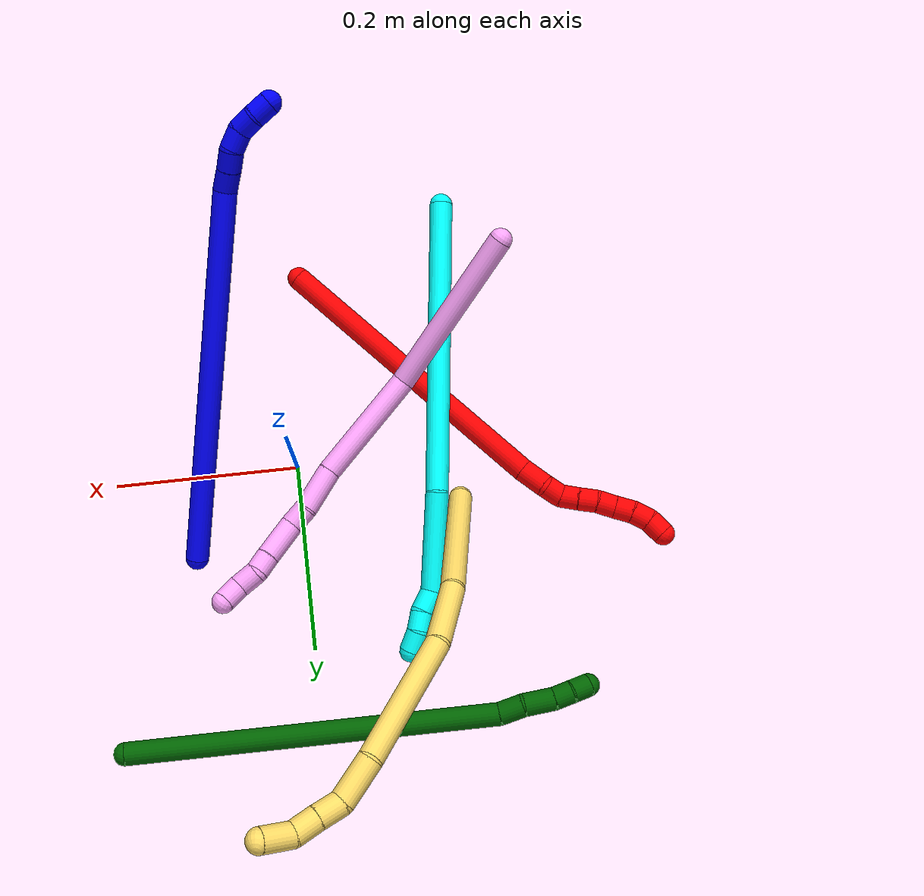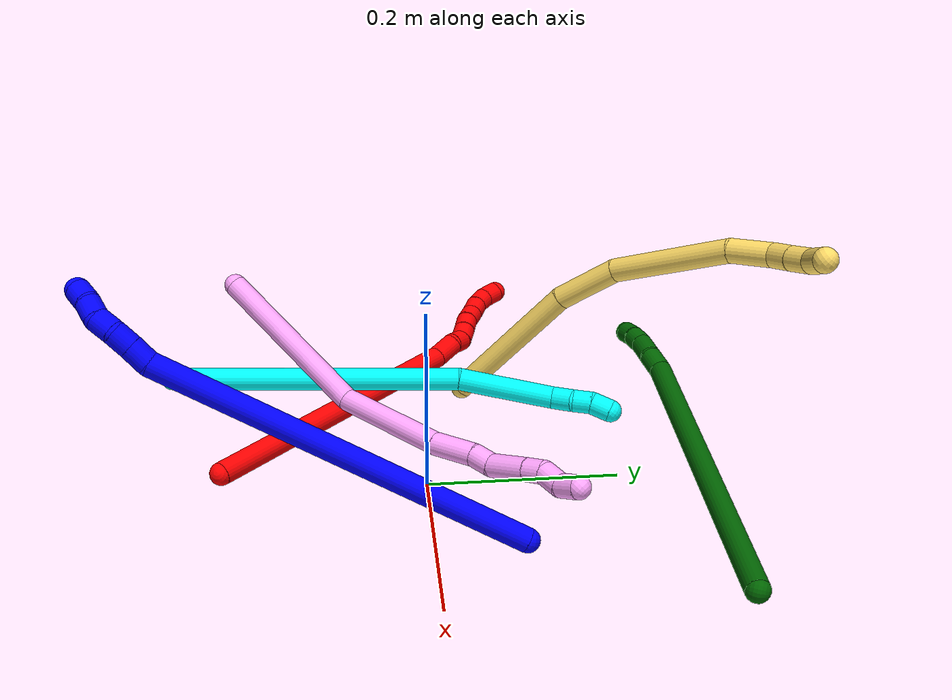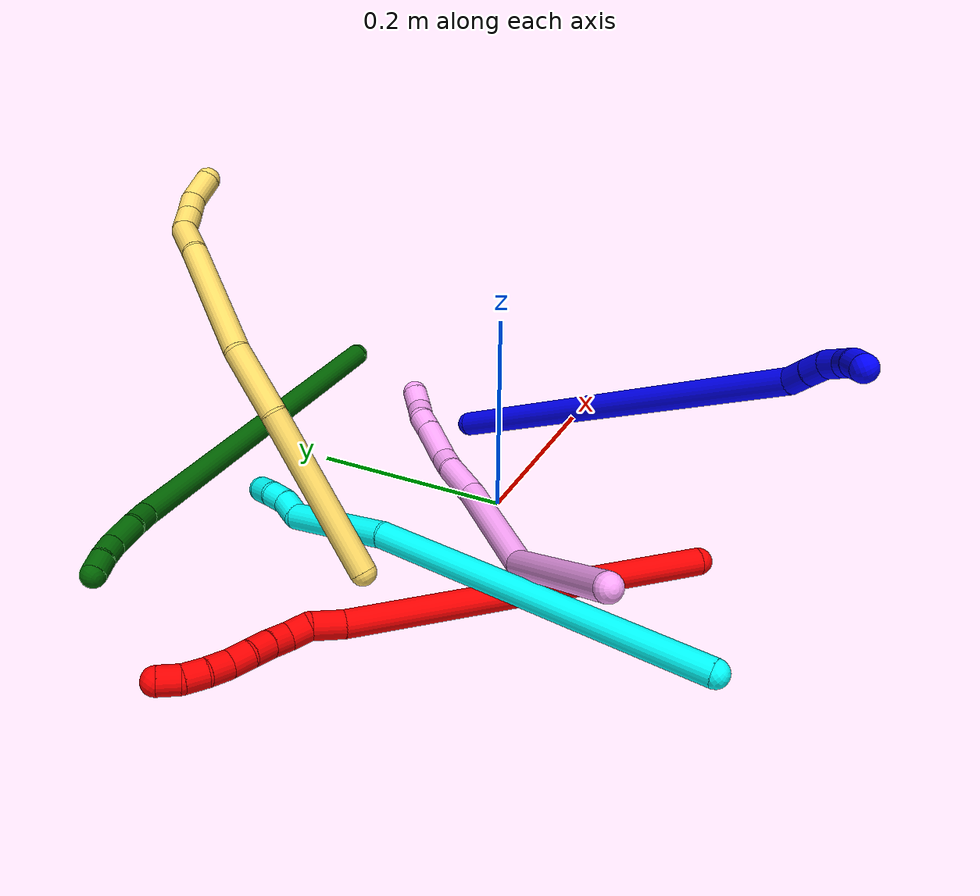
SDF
<sdf version="1.7">
 <world name="default">
  <plugin name="TubeGeneratorPlugin" filename="libtube_generator_plugin.so"/>
  <model name="photoneo_s_sensor">
   <static>1</static>
   <pose>0 0 2 1.57079 1.57079 3.14159</pose>
   <link name="link">
    <inertial><mass>0.1</mass></inertial>
    <sensor name="sensor" type="depth">
     <update_rate>30</update_rate>
     <camera>
      <horizontal_fov>1.22</horizontal_fov>
      <image><width>1920</width><height>1200</height><format>B8G8R8</format></image>
      <clip><near>0.1</near><far>4</far></clip>
      <depth_camera><output>points</output></depth_camera>
     </camera>
     <plugin name="camera_plugin" filename="libgazebo_ros_depth_camera.so">
      <baseline>0.2</baseline>
      <alwaysOn>1</alwaysOn>
      <updateRate>0.0</updateRate>
      <cameraName>camera_ir</cameraName>
      <imageTopicName>/camera/color/image_raw</imageTopicName>
      <cameraInfoTopicName>/camera/color/camera_info</cameraInfoTopicName>
      <depthImageTopicName>/camera/depth/image_raw</depthImageTopicName>
      <depthImageCameraInfoTopicName>/camera/depth/camera_info</depthImageCameraInfoTopicName>
      <pointCloudTopicName>/camera/depth/points</pointCloudTopicName>
      <frameName>fr_optical</frameName>
      <pointCloudCutoff>0.1</pointCloudCutoff>
      <pointCloudCutoffMax>2.0</pointCloudCutoffMax>
      <distortionK1>0</distortionK1>
      <distortionK2>0</distortionK2>
      <distortionK3>0</distortionK3>
      <distortionT1>0</distortionT1>
      <distortionT2>0</distortionT2>
      <CxPrime>0</CxPrime>
      <Cx>0</Cx>
      <Cy>0</Cy>
      <focalLength>0</focalLength>
      <hackBaseline>0</hackBaseline>
     </plugin>
    </sensor>
   </link>
  </model>
  <gravity>0 0 -9.8</gravity>
  <magnetic_field>6e-06 2.3e-05 -4.2e-05</magnetic_field>
  <atmosphere type="adiabatic"/>
  <physics name="default_physics" default="0" type="ode">
   <max_step_size>0.003</max_step_size>
   <real_time_factor>1</real_time_factor>
   <real_time_update_rate>1000</real_time_update_rate>
   <max_contacts>10000</max_contacts>
   <ode>
    <solver>
     <type>quick</type>
     <iters>100</iters>
     <sor>1.3</sor>
     <use_dynamic_moi_rescaling>0</use_dynamic_moi_rescaling>
    </solver>
    <constraints>
     <contact_max_correcting_vel>0</contact_max_correcting_vel>
     <contact_surface_layer>0.001</contact_surface_layer>
     <cfm>0</cfm>
     <erp>0.2</erp>
    </constraints>
   </ode>
  </physics>
  <scene><ambient>0.4 0.4 0.4 1</ambient><background>0.7 0.7 0.7 1</background><shadows>0</shadows></scene>
  <audio><device>default</device></audio>
  <spherical_coordinates>
   <surface_model>EARTH_WGS84</surface_model>
   <latitude_deg>0</latitude_deg>
   <longitude_deg>0</longitude_deg>
   <elevation>0</elevation>
   <heading_deg>0</heading_deg>
  </spherical_coordinates>
  <model name="bin">
   <static>1</static>
   <link name="bottom">
    <collision name="collision-bottom">
     <pose>0 0 -0.01 0 -0 0</pose>
     <geometry><box><size>0.8 0.6 0.02</size></box></geometry>
     <surface>
      <friction><ode><mu>100</mu><mu2>100</mu2></ode></friction>
      <contact><collide_bitmask>65535</collide_bitmask></contact>
     </surface>
    </collision>
   </link>
   <link name="west_wall">
    <collision name="collision-west_wall">
     <pose>-0.41 0 0.1 0 -0 0</pose>
     <geometry><box><size>0.02 0.6 0.2</size></box></geometry>
     <surface>
      <friction><ode><mu>100</mu><mu2>100</mu2></ode></friction>
      <contact><collide_bitmask>65535</collide_bitmask></contact>
     </surface>
    </collision>
   </link>
   <link name="east_wall">
    <collision name="collision-east_wall">
     <pose>0.41 0 0.1 0 -0 0</pose>
     <geometry><box><size>0.02 0.6 0.2</size></box></geometry>
     <surface>
      <friction><ode><mu>100</mu><mu2>100</mu2></ode></friction>
      <contact><collide_bitmask>65535</collide_bitmask></contact>
     </surface>
    </collision>
   </link>
   <link name="south_wall">
    <collision name="collision-south_wall">
     <pose>0 -0.31 0.1 0 -0 0</pose>
     <geometry><box><size>0.8 0.02 0.2</size></box></geometry>
     <surface>
      <friction><ode><mu>100</mu><mu2>100</mu2></ode></friction>
      <contact><collide_bitmask>65535</collide_bitmask></contact>
     </surface>
    </collision>
   </link>
   <link name="north_wall">
    <collision name="collision-north_wall">
     <pose>0 0.31 0.1 0 -0 0</pose>
     <geometry><box><size>0.8 0.02 0.2</size></box></geometry>
     <surface>
      <friction><ode><mu>100</mu><mu2>100</mu2></ode></friction>
      <contact><collide_bitmask>65535</collide_bitmask></contact>
     </surface>
    </collision>
   </link>
  </model>
  <model name="1">
   <static>0</static>
   <link name="1">
    <collision name="collision-cylinder-e_1_1_4">
     <pose>-0.019477 -0.105853 0.166045 0.567536 -0.09859 -0.028774</pose>
     <geometry><cylinder><radius>0.0125</radius><length>0.395754</length></cylinder></geometry>
     <surface>
      <friction><ode><mu>1.16</mu><mu2>1.16</mu2><slip1>0</slip1><slip2>0</slip2></ode></friction>
      <contact><ode><kp>1e+06</kp><kd>1</kd><max_vel>0</max_vel><min_depth>0.001</min_depth></ode></contact>
     </surface>
    </collision>
    <visual name="visual-cylinder-e_1_1_4">
     <pose>-0.019477 -0.105853 0.166045 0.567536 -0.09859 -0.028774</pose>
     <geometry><cylinder><radius>0.0125</radius><length>0.395754</length></cylinder></geometry>
     <material><ambient>0 0 1 1</ambient></material>
    </visual>
    <collision name="collision-cylinder-e_2_4_5">
     <pose>-0.043565 -0.217752 0.340475 0.624657 -0.419572 -0.137286</pose>
     <geometry><cylinder><radius>0.0125</radius><length>0.022637</length></cylinder></geometry>
     <surface>
      <friction><ode><mu>1.16</mu><mu2>1.16</mu2><slip1>0</slip1><slip2>0</slip2></ode></friction>
      <contact><ode><kp>1e+06</kp><kd>1</kd><max_vel>0</max_vel><min_depth>0.001</min_depth></ode></contact>
     </surface>
    </collision>
    <visual name="visual-cylinder-e_2_4_5">
     <pose>-0.043565 -0.217752 0.340475 0.624657 -0.419572 -0.137286</pose>
     <geometry><cylinder><radius>0.0125</radius><length>0.022637</length></cylinder></geometry>
     <material><ambient>0 0 1 1</ambient></material>
    </visual>
    <collision name="collision-cylinder-e_3_5_6">
     <pose>-0.052027 -0.229057 0.356844 0.582485 -0.382924 -0.116081</pose>
     <geometry><cylinder><radius>0.0125</radius><length>0.020616</length></cylinder></geometry>
     <surface>
      <friction><ode><mu>1.16</mu><mu2>1.16</mu2><slip1>0</slip1><slip2>0</slip2></ode></friction>
      <contact><ode><kp>1e+06</kp><kd>1</kd><max_vel>0</max_vel><min_depth>0.001</min_depth></ode></contact>
     </surface>
    </collision>
    <visual name="visual-cylinder-e_3_5_6">
     <pose>-0.052027 -0.229057 0.356844 0.582485 -0.382924 -0.116081</pose>
     <geometry><cylinder><radius>0.0125</radius><length>0.020616</length></cylinder></geometry>
     <material><ambient>0 0 1 1</ambient></material>
    </visual>
    <collision name="collision-cylinder-e_4_6_7">
     <pose>-0.058183 -0.242253 0.371256 0.890113 -0.22199 -0.10622</pose>
     <geometry><cylinder><radius>0.0125</radius><length>0.020939</length></cylinder></geometry>
     <surface>
      <friction><ode><mu>1.16</mu><mu2>1.16</mu2><slip1>0</slip1><slip2>0</slip2></ode></friction>
      <contact><ode><kp>1e+06</kp><kd>1</kd><max_vel>0</max_vel><min_depth>0.001</min_depth></ode></contact>
     </surface>
    </collision>
    <visual name="visual-cylinder-e_4_6_7">
     <pose>-0.058183 -0.242253 0.371256 0.890113 -0.22199 -0.10622</pose>
     <geometry><cylinder><radius>0.0125</radius><length>0.020939</length></cylinder></geometry>
     <material><ambient>0 0 1 1</ambient></material>
    </visual>
    <collision name="collision-cylinder-e_5_7_8">
     <pose>-0.064716 -0.258804 0.380503 1.25443 -0.436388 -0.318711</pose>
     <geometry><cylinder><radius>0.0125</radius><length>0.020004</length></cylinder></geometry>
     <surface>
      <friction><ode><mu>1.16</mu><mu2>1.16</mu2><slip1>0</slip1><slip2>0</slip2></ode></friction>
      <contact><ode><kp>1e+06</kp><kd>1</kd><max_vel>0</max_vel><min_depth>0.001</min_depth></ode></contact>
     </surface>
    </collision>
    <visual name="visual-cylinder-e_5_7_8">
     <pose>-0.064716 -0.258804 0.380503 1.25443 -0.436388 -0.318711</pose>
     <geometry><cylinder><radius>0.0125</radius><length>0.020004</length></cylinder></geometry>
     <material><ambient>0 0 1 1</ambient></material>
    </visual>
    <collision name="collision-cylinder-e_6_8_2">
     <pose>-0.070912 -0.27694 0.385771 1.31911 -0.197647 -0.153453</pose>
     <geometry><cylinder><radius>0.0125</radius><length>0.020051</length></cylinder></geometry>
     <surface>
      <friction><ode><mu>1.16</mu><mu2>1.16</mu2><slip1>0</slip1><slip2>0</slip2></ode></friction>
      <contact><ode><kp>1e+06</kp><kd>1</kd><max_vel>0</max_vel><min_depth>0.001</min_depth></ode></contact>
     </surface>
    </collision>
    <visual name="visual-cylinder-e_6_8_2">
     <pose>-0.070912 -0.27694 0.385771 1.31911 -0.197647 -0.153453</pose>
     <geometry><cylinder><radius>0.0125</radius><length>0.020051</length></cylinder></geometry>
     <material><ambient>0 0 1 1</ambient></material>
    </visual>
    <collision name="collision-sphere-2">
     <pose>-0.072881 -0.28646 0.388219 0 -0 0</pose>
     <geometry><sphere><radius>0.0125</radius></sphere></geometry>
     <surface>
      <friction><ode><mu>1.16</mu><mu2>1.16</mu2><slip1>0</slip1><slip2>0</slip2></ode></friction>
      <contact><ode><kp>1e+06</kp><kd>1</kd><max_vel>0</max_vel><min_depth>0.001</min_depth></ode></contact>
     </surface>
    </collision>
    <visual name="visual-sphere-2">
     <pose>-0.072881 -0.28646 0.388219 0 -0 0</pose>
     <geometry><sphere><radius>0.0125</radius></sphere></geometry>
     <material><ambient>0 0 1 1</ambient></material>
    </visual>
    <collision name="collision-sphere-4">
     <pose>-0.038954 -0.211707 0.33209 0 -0 0</pose>
     <geometry><sphere><radius>0.0125</radius></sphere></geometry>
     <surface>
      <friction><ode><mu>1.16</mu><mu2>1.16</mu2><slip1>0</slip1><slip2>0</slip2></ode></friction>
      <contact><ode><kp>1e+06</kp><kd>1</kd><max_vel>0</max_vel><min_depth>0.001</min_depth></ode></contact>
     </surface>
    </collision>
    <visual name="visual-sphere-4">
     <pose>-0.038954 -0.211707 0.33209 0 -0 0</pose>
     <geometry><sphere><radius>0.0125</radius></sphere></geometry>
     <material><ambient>0 0 1 1</ambient></material>
    </visual>
    <collision name="collision-sphere-1">
     <geometry><sphere><radius>0.0125</radius></sphere></geometry>
     <surface>
      <friction><ode><mu>1.16</mu><mu2>1.16</mu2><slip1>0</slip1><slip2>0</slip2></ode></friction>
      <contact><ode><kp>1e+06</kp><kd>1</kd><max_vel>0</max_vel><min_depth>0.001</min_depth></ode></contact>
     </surface>
    </collision>
    <visual name="visual-sphere-1">
     <geometry><sphere><radius>0.0125</radius></sphere></geometry>
     <material><ambient>0 0 1 1</ambient></material>
    </visual>
    <collision name="collision-sphere-8">
     <pose>-0.068944 -0.267419 0.383323 0 -0 0</pose>
     <geometry><sphere><radius>0.0125</radius></sphere></geometry>
     <surface>
      <friction><ode><mu>1.16</mu><mu2>1.16</mu2><slip1>0</slip1><slip2>0</slip2></ode></friction>
      <contact><ode><kp>1e+06</kp><kd>1</kd><max_vel>0</max_vel><min_depth>0.001</min_depth></ode></contact>
     </surface>
    </collision>
    <visual name="visual-sphere-8">
     <pose>-0.068944 -0.267419 0.383323 0 -0 0</pose>
     <geometry><sphere><radius>0.0125</radius></sphere></geometry>
     <material><ambient>0 0 1 1</ambient></material>
    </visual>
    <collision name="collision-sphere-5">
     <pose>-0.048176 -0.223797 0.34886 0 -0 0</pose>
     <geometry><sphere><radius>0.0125</radius></sphere></geometry>
     <surface>
      <friction><ode><mu>1.16</mu><mu2>1.16</mu2><slip1>0</slip1><slip2>0</slip2></ode></friction>
      <contact><ode><kp>1e+06</kp><kd>1</kd><max_vel>0</max_vel><min_depth>0.001</min_depth></ode></contact>
     </surface>
    </collision>
    <visual name="visual-sphere-5">
     <pose>-0.048176 -0.223797 0.34886 0 -0 0</pose>
     <geometry><sphere><radius>0.0125</radius></sphere></geometry>
     <material><ambient>0 0 1 1</ambient></material>
    </visual>
    <collision name="collision-sphere-6">
     <pose>-0.055878 -0.234316 0.364829 0 -0 0</pose>
     <geometry><sphere><radius>0.0125</radius></sphere></geometry>
     <surface>
      <friction><ode><mu>1.16</mu><mu2>1.16</mu2><slip1>0</slip1><slip2>0</slip2></ode></friction>
      <contact><ode><kp>1e+06</kp><kd>1</kd><max_vel>0</max_vel><min_depth>0.001</min_depth></ode></contact>
     </surface>
    </collision>
    <visual name="visual-sphere-6">
     <pose>-0.055878 -0.234316 0.364829 0 -0 0</pose>
     <geometry><sphere><radius>0.0125</radius></sphere></geometry>
     <material><ambient>0 0 1 1</ambient></material>
    </visual>
    <collision name="collision-sphere-7">
     <pose>-0.060489 -0.250189 0.377683 0 -0 0</pose>
     <geometry><sphere><radius>0.0125</radius></sphere></geometry>
     <surface>
      <friction><ode><mu>1.16</mu><mu2>1.16</mu2><slip1>0</slip1><slip2>0</slip2></ode></friction>
      <contact><ode><kp>1e+06</kp><kd>1</kd><max_vel>0</max_vel><min_depth>0.001</min_depth></ode></contact>
     </surface>
    </collision>
    <visual name="visual-sphere-7">
     <pose>-0.060489 -0.250189 0.377683 0 -0 0</pose>
     <geometry><sphere><radius>0.0125</radius></sphere></geometry>
     <material><ambient>0 0 1 1</ambient></material>
    </visual>
    <inertial>
     <pose>-0.027403 -0.134692 0.207794 0 -0 0</pose>
     <mass>0.5</mass>
     <inertia>
      <ixx>0.005006</ixx>
      <ixy>0</ixy>
      <ixz>0</ixz>
      <iyy>0.004208</iyy>
      <iyz>0</iyz>
      <izz>0.00332</izz>
     </inertia>
    </inertial>
   </link>
   <pose>0.116937 0.088516 0.011497 0.10706 1.12158 -1.03496</pose>
  </model>
  <model name="2">
   <static>0</static>
   <link name="2">
    <collision name="collision-cylinder-e_1_1_4">
     <pose>-0.106096 0.058304 0.111728 -0.480962 -0.699748 0.178484</pose>
     <geometry><cylinder><radius>0.0125</radius><length>0.329477</length></cylinder></geometry>
     <surface>
      <friction><ode><mu>1.16</mu><mu2>1.16</mu2><slip1>0</slip1><slip2>0</slip2></ode></friction>
      <contact><ode><kp>1e+06</kp><kd>1</kd><max_vel>0</max_vel><min_depth>0.001</min_depth></ode></contact>
     </surface>
    </collision>
    <visual name="visual-cylinder-e_1_1_4">
     <pose>-0.106096 0.058304 0.111728 -0.480962 -0.699748 0.178484</pose>
     <geometry><cylinder><radius>0.0125</radius><length>0.329477</length></cylinder></geometry>
     <material><ambient>1 0 0 1</ambient></material>
    </visual>
    <collision name="collision-cylinder-e_2_4_5">
     <pose>-0.222048 0.124233 0.231872 -0.736162 -0.714769 0.286057</pose>
     <geometry><cylinder><radius>0.0125</radius><length>0.030076</length></cylinder></geometry>
     <surface>
      <friction><ode><mu>1.16</mu><mu2>1.16</mu2><slip1>0</slip1><slip2>0</slip2></ode></friction>
      <contact><ode><kp>1e+06</kp><kd>1</kd><max_vel>0</max_vel><min_depth>0.001</min_depth></ode></contact>
     </surface>
    </collision>
    <visual name="visual-cylinder-e_2_4_5">
     <pose>-0.222048 0.124233 0.231872 -0.736162 -0.714769 0.286057</pose>
     <geometry><cylinder><radius>0.0125</radius><length>0.030076</length></cylinder></geometry>
     <material><ambient>1 0 0 1</ambient></material>
    </visual>
    <collision name="collision-cylinder-e_3_5_6">
     <pose>-0.236366 0.134947 0.248896 -0.344458 -0.453863 0.080291</pose>
     <geometry><cylinder><radius>0.0125</radius><length>0.020349</length></cylinder></geometry>
     <surface>
      <friction><ode><mu>1.16</mu><mu2>1.16</mu2><slip1>0</slip1><slip2>0</slip2></ode></friction>
      <contact><ode><kp>1e+06</kp><kd>1</kd><max_vel>0</max_vel><min_depth>0.001</min_depth></ode></contact>
     </surface>
    </collision>
    <visual name="visual-cylinder-e_3_5_6">
     <pose>-0.236366 0.134947 0.248896 -0.344458 -0.453863 0.080291</pose>
     <geometry><cylinder><radius>0.0125</radius><length>0.020349</length></cylinder></geometry>
     <material><ambient>1 0 0 1</ambient></material>
    </visual>
    <collision name="collision-cylinder-e_4_6_7">
     <pose>-0.243364 0.145363 0.263833 -0.858365 -0.256271 0.117787</pose>
     <geometry><cylinder><radius>0.0125</radius><length>0.020021</length></cylinder></geometry>
     <surface>
      <friction><ode><mu>1.16</mu><mu2>1.16</mu2><slip1>0</slip1><slip2>0</slip2></ode></friction>
      <contact><ode><kp>1e+06</kp><kd>1</kd><max_vel>0</max_vel><min_depth>0.001</min_depth></ode></contact>
     </surface>
    </collision>
    <visual name="visual-cylinder-e_4_6_7">
     <pose>-0.243364 0.145363 0.263833 -0.858365 -0.256271 0.117787</pose>
     <geometry><cylinder><radius>0.0125</radius><length>0.020021</length></cylinder></geometry>
     <material><ambient>1 0 0 1</ambient></material>
    </visual>
    <collision name="collision-cylinder-e_5_7_8">
     <pose>-0.247934 0.159846 0.276884 -0.816632 -0.204169 0.08858</pose>
     <geometry><cylinder><radius>0.0125</radius><length>0.020049</length></cylinder></geometry>
     <surface>
      <friction><ode><mu>1.16</mu><mu2>1.16</mu2><slip1>0</slip1><slip2>0</slip2></ode></friction>
      <contact><ode><kp>1e+06</kp><kd>1</kd><max_vel>0</max_vel><min_depth>0.001</min_depth></ode></contact>
     </surface>
    </collision>
    <visual name="visual-cylinder-e_5_7_8">
     <pose>-0.247934 0.159846 0.276884 -0.816632 -0.204169 0.08858</pose>
     <geometry><cylinder><radius>0.0125</radius><length>0.020049</length></cylinder></geometry>
     <material><ambient>1 0 0 1</ambient></material>
    </visual>
    <collision name="collision-cylinder-e_6_8_9">
     <pose>-0.253025 0.17264 0.291282 -0.633604 -0.310664 0.102586</pose>
     <geometry><cylinder><radius>0.0125</radius><length>0.02001</length></cylinder></geometry>
     <surface>
      <friction><ode><mu>1.16</mu><mu2>1.16</mu2><slip1>0</slip1><slip2>0</slip2></ode></friction>
      <contact><ode><kp>1e+06</kp><kd>1</kd><max_vel>0</max_vel><min_depth>0.001</min_depth></ode></contact>
     </surface>
    </collision>
    <visual name="visual-cylinder-e_6_8_9">
     <pose>-0.253025 0.17264 0.291282 -0.633604 -0.310664 0.102586</pose>
     <geometry><cylinder><radius>0.0125</radius><length>0.02001</length></cylinder></geometry>
     <material><ambient>1 0 0 1</ambient></material>
    </visual>
    <collision name="collision-cylinder-e_7_9_10">
     <pose>-0.259458 0.184968 0.305593 -0.789434 -0.344067 0.14451</pose>
     <geometry><cylinder><radius>0.0125</radius><length>0.020011</length></cylinder></geometry>
     <surface>
      <friction><ode><mu>1.16</mu><mu2>1.16</mu2><slip1>0</slip1><slip2>0</slip2></ode></friction>
      <contact><ode><kp>1e+06</kp><kd>1</kd><max_vel>0</max_vel><min_depth>0.001</min_depth></ode></contact>
     </surface>
    </collision>
    <visual name="visual-cylinder-e_7_9_10">
     <pose>-0.259458 0.184968 0.305593 -0.789434 -0.344067 0.14451</pose>
     <geometry><cylinder><radius>0.0125</radius><length>0.020011</length></cylinder></geometry>
     <material><ambient>1 0 0 1</ambient></material>
    </visual>
    <collision name="collision-cylinder-e_8_10_11">
     <pose>-0.267691 0.196965 0.319172 -0.652744 -0.507088 0.174965</pose>
     <geometry><cylinder><radius>0.0125</radius><length>0.020004</length></cylinder></geometry>
     <surface>
      <friction><ode><mu>1.16</mu><mu2>1.16</mu2><slip1>0</slip1><slip2>0</slip2></ode></friction>
      <contact><ode><kp>1e+06</kp><kd>1</kd><max_vel>0</max_vel><min_depth>0.001</min_depth></ode></contact>
     </surface>
    </collision>
    <visual name="visual-cylinder-e_8_10_11">
     <pose>-0.267691 0.196965 0.319172 -0.652744 -0.507088 0.174965</pose>
     <geometry><cylinder><radius>0.0125</radius><length>0.020004</length></cylinder></geometry>
     <material><ambient>1 0 0 1</ambient></material>
    </visual>
    <collision name="collision-cylinder-e_9_11_2">
     <pose>-0.279831 0.205835 0.331975 -0.546119 -0.815727 0.240848</pose>
     <geometry><cylinder><radius>0.0125</radius><length>0.020003</length></cylinder></geometry>
     <surface>
      <friction><ode><mu>1.16</mu><mu2>1.16</mu2><slip1>0</slip1><slip2>0</slip2></ode></friction>
      <contact><ode><kp>1e+06</kp><kd>1</kd><max_vel>0</max_vel><min_depth>0.001</min_depth></ode></contact>
     </surface>
    </collision>
    <visual name="visual-cylinder-e_9_11_2">
     <pose>-0.279831 0.205835 0.331975 -0.546119 -0.815727 0.240848</pose>
     <geometry><cylinder><radius>0.0125</radius><length>0.020003</length></cylinder></geometry>
     <material><ambient>1 0 0 1</ambient></material>
    </visual>
    <collision name="collision-sphere-2">
     <pose>-0.287115 0.209395 0.337833 0 -0 0</pose>
     <geometry><sphere><radius>0.0125</radius></sphere></geometry>
     <surface>
      <friction><ode><mu>1.16</mu><mu2>1.16</mu2><slip1>0</slip1><slip2>0</slip2></ode></friction>
      <contact><ode><kp>1e+06</kp><kd>1</kd><max_vel>0</max_vel><min_depth>0.001</min_depth></ode></contact>
     </surface>
    </collision>
    <visual name="visual-sphere-2">
     <pose>-0.287115 0.209395 0.337833 0 -0 0</pose>
     <geometry><sphere><radius>0.0125</radius></sphere></geometry>
     <material><ambient>1 0 0 1</ambient></material>
    </visual>
    <collision name="collision-sphere-11">
     <pose>-0.272548 0.202275 0.326118 0 -0 0</pose>
     <geometry><sphere><radius>0.0125</radius></sphere></geometry>
     <surface>
      <friction><ode><mu>1.16</mu><mu2>1.16</mu2><slip1>0</slip1><slip2>0</slip2></ode></friction>
      <contact><ode><kp>1e+06</kp><kd>1</kd><max_vel>0</max_vel><min_depth>0.001</min_depth></ode></contact>
     </surface>
    </collision>
    <visual name="visual-sphere-11">
     <pose>-0.272548 0.202275 0.326118 0 -0 0</pose>
     <geometry><sphere><radius>0.0125</radius></sphere></geometry>
     <material><ambient>1 0 0 1</ambient></material>
    </visual>
    <collision name="collision-sphere-10">
     <pose>-0.262833 0.191655 0.312226 0 -0 0</pose>
     <geometry><sphere><radius>0.0125</radius></sphere></geometry>
     <surface>
      <friction><ode><mu>1.16</mu><mu2>1.16</mu2><slip1>0</slip1><slip2>0</slip2></ode></friction>
      <contact><ode><kp>1e+06</kp><kd>1</kd><max_vel>0</max_vel><min_depth>0.001</min_depth></ode></contact>
     </surface>
    </collision>
    <visual name="visual-sphere-10">
     <pose>-0.262833 0.191655 0.312226 0 -0 0</pose>
     <geometry><sphere><radius>0.0125</radius></sphere></geometry>
     <material><ambient>1 0 0 1</ambient></material>
    </visual>
    <collision name="collision-sphere-9">
     <pose>-0.256083 0.17828 0.29896 0 -0 0</pose>
     <geometry><sphere><radius>0.0125</radius></sphere></geometry>
     <surface>
      <friction><ode><mu>1.16</mu><mu2>1.16</mu2><slip1>0</slip1><slip2>0</slip2></ode></friction>
      <contact><ode><kp>1e+06</kp><kd>1</kd><max_vel>0</max_vel><min_depth>0.001</min_depth></ode></contact>
     </surface>
    </collision>
    <visual name="visual-sphere-9">
     <pose>-0.256083 0.17828 0.29896 0 -0 0</pose>
     <geometry><sphere><radius>0.0125</radius></sphere></geometry>
     <material><ambient>1 0 0 1</ambient></material>
    </visual>
    <collision name="collision-sphere-4">
     <pose>-0.212191 0.116607 0.223456 0 -0 0</pose>
     <geometry><sphere><radius>0.0125</radius></sphere></geometry>
     <surface>
      <friction><ode><mu>1.16</mu><mu2>1.16</mu2><slip1>0</slip1><slip2>0</slip2></ode></friction>
      <contact><ode><kp>1e+06</kp><kd>1</kd><max_vel>0</max_vel><min_depth>0.001</min_depth></ode></contact>
     </surface>
    </collision>
    <visual name="visual-sphere-4">
     <pose>-0.212191 0.116607 0.223456 0 -0 0</pose>
     <geometry><sphere><radius>0.0125</radius></sphere></geometry>
     <material><ambient>1 0 0 1</ambient></material>
    </visual>
    <collision name="collision-sphere-1">
     <geometry><sphere><radius>0.0125</radius></sphere></geometry>
     <surface>
      <friction><ode><mu>1.16</mu><mu2>1.16</mu2><slip1>0</slip1><slip2>0</slip2></ode></friction>
      <contact><ode><kp>1e+06</kp><kd>1</kd><max_vel>0</max_vel><min_depth>0.001</min_depth></ode></contact>
     </surface>
    </collision>
    <visual name="visual-sphere-1">
     <geometry><sphere><radius>0.0125</radius></sphere></geometry>
     <material><ambient>1 0 0 1</ambient></material>
    </visual>
    <collision name="collision-sphere-8">
     <pose>-0.249966 0.167 0.283605 0 -0 0</pose>
     <geometry><sphere><radius>0.0125</radius></sphere></geometry>
     <surface>
      <friction><ode><mu>1.16</mu><mu2>1.16</mu2><slip1>0</slip1><slip2>0</slip2></ode></friction>
      <contact><ode><kp>1e+06</kp><kd>1</kd><max_vel>0</max_vel><min_depth>0.001</min_depth></ode></contact>
     </surface>
    </collision>
    <visual name="visual-sphere-8">
     <pose>-0.249966 0.167 0.283605 0 -0 0</pose>
     <geometry><sphere><radius>0.0125</radius></sphere></geometry>
     <material><ambient>1 0 0 1</ambient></material>
    </visual>
    <collision name="collision-sphere-5">
     <pose>-0.231905 0.131859 0.240289 0 -0 0</pose>
     <geometry><sphere><radius>0.0125</radius></sphere></geometry>
     <surface>
      <friction><ode><mu>1.16</mu><mu2>1.16</mu2><slip1>0</slip1><slip2>0</slip2></ode></friction>
      <contact><ode><kp>1e+06</kp><kd>1</kd><max_vel>0</max_vel><min_depth>0.001</min_depth></ode></contact>
     </surface>
    </collision>
    <visual name="visual-sphere-5">
     <pose>-0.231905 0.131859 0.240289 0 -0 0</pose>
     <geometry><sphere><radius>0.0125</radius></sphere></geometry>
     <material><ambient>1 0 0 1</ambient></material>
    </visual>
    <collision name="collision-sphere-6">
     <pose>-0.240827 0.138035 0.257503 0 -0 0</pose>
     <geometry><sphere><radius>0.0125</radius></sphere></geometry>
     <surface>
      <friction><ode><mu>1.16</mu><mu2>1.16</mu2><slip1>0</slip1><slip2>0</slip2></ode></friction>
      <contact><ode><kp>1e+06</kp><kd>1</kd><max_vel>0</max_vel><min_depth>0.001</min_depth></ode></contact>
     </surface>
    </collision>
    <visual name="visual-sphere-6">
     <pose>-0.240827 0.138035 0.257503 0 -0 0</pose>
     <geometry><sphere><radius>0.0125</radius></sphere></geometry>
     <material><ambient>1 0 0 1</ambient></material>
    </visual>
    <collision name="collision-sphere-7">
     <pose>-0.245901 0.152691 0.270163 0 -0 0</pose>
     <geometry><sphere><radius>0.0125</radius></sphere></geometry>
     <surface>
      <friction><ode><mu>1.16</mu><mu2>1.16</mu2><slip1>0</slip1><slip2>0</slip2></ode></friction>
      <contact><ode><kp>1e+06</kp><kd>1</kd><max_vel>0</max_vel><min_depth>0.001</min_depth></ode></contact>
     </surface>
    </collision>
    <visual name="visual-sphere-7">
     <pose>-0.245901 0.152691 0.270163 0 -0 0</pose>
     <geometry><sphere><radius>0.0125</radius></sphere></geometry>
     <material><ambient>1 0 0 1</ambient></material>
    </visual>
    <inertial>
     <pose>-0.15499 0.094041 0.169306 0 -0 0</pose>
     <mass>0.5</mass>
     <inertia>
      <ixx>0.002651</ixx>
      <ixy>0</ixy>
      <ixz>0</ixz>
      <iyy>0.003206</iyy>
      <iyz>0</iyz>
      <izz>0.000894</izz>
     </inertia>
    </inertial>
   </link>
   <pose>-0.022433 -0.212482 0.011498 2.32735 0.312604 -1.65216</pose>
  </model>
  <model name="3">
   <static>0</static>
   <link name="3">
    <collision name="collision-cylinder-e_1_1_4">
     <pose>0.027266 0.113089 -0.112978 -2.3557 0.168945 -0.403013</pose>
     <geometry><cylinder><radius>0.0125</radius><length>0.324324</length></cylinder></geometry>
     <surface>
      <friction><ode><mu>1.16</mu><mu2>1.16</mu2><slip1>0</slip1><slip2>0</slip2></ode></friction>
      <contact><ode><kp>1e+06</kp><kd>1</kd><max_vel>0</max_vel><min_depth>0.001</min_depth></ode></contact>
     </surface>
    </collision>
    <visual name="visual-cylinder-e_1_1_4">
     <pose>0.027266 0.113089 -0.112978 -2.3557 0.168945 -0.403013</pose>
     <geometry><cylinder><radius>0.0125</radius><length>0.324324</length></cylinder></geometry>
     <material><ambient>0.003922 1 0.996078 1</ambient></material>
    </visual>
    <collision name="collision-cylinder-e_2_4_5">
     <pose>0.065338 0.254726 -0.270189 -2.56844 0.202434 -0.663805</pose>
     <geometry><cylinder><radius>0.0125</radius><length>0.107486</length></cylinder></geometry>
     <surface>
      <friction><ode><mu>1.16</mu><mu2>1.16</mu2><slip1>0</slip1><slip2>0</slip2></ode></friction>
      <contact><ode><kp>1e+06</kp><kd>1</kd><max_vel>0</max_vel><min_depth>0.001</min_depth></ode></contact>
     </surface>
    </collision>
    <visual name="visual-cylinder-e_2_4_5">
     <pose>0.065338 0.254726 -0.270189 -2.56844 0.202434 -0.663805</pose>
     <geometry><cylinder><radius>0.0125</radius><length>0.107486</length></cylinder></geometry>
     <material><ambient>0.003922 1 0.996078 1</ambient></material>
    </visual>
    <collision name="collision-cylinder-e_3_5_6">
     <pose>0.083177 0.291511 -0.320659 -2.21902 0.597701 -1.10971</pose>
     <geometry><cylinder><radius>0.0125</radius><length>0.024997</length></cylinder></geometry>
     <surface>
      <friction><ode><mu>1.16</mu><mu2>1.16</mu2><slip1>0</slip1><slip2>0</slip2></ode></friction>
      <contact><ode><kp>1e+06</kp><kd>1</kd><max_vel>0</max_vel><min_depth>0.001</min_depth></ode></contact>
     </surface>
    </collision>
    <visual name="visual-cylinder-e_3_5_6">
     <pose>0.083177 0.291511 -0.320659 -2.21902 0.597701 -1.10971</pose>
     <geometry><cylinder><radius>0.0125</radius><length>0.024997</length></cylinder></geometry>
     <material><ambient>0.003922 1 0.996078 1</ambient></material>
    </visual>
    <collision name="collision-cylinder-e_4_6_7">
     <pose>0.093706 0.306474 -0.333925 -2.37806 0.344957 -0.818834</pose>
     <geometry><cylinder><radius>0.0125</radius><length>0.020675</length></cylinder></geometry>
     <surface>
      <friction><ode><mu>1.16</mu><mu2>1.16</mu2><slip1>0</slip1><slip2>0</slip2></ode></friction>
      <contact><ode><kp>1e+06</kp><kd>1</kd><max_vel>0</max_vel><min_depth>0.001</min_depth></ode></contact>
     </surface>
    </collision>
    <visual name="visual-cylinder-e_4_6_7">
     <pose>0.093706 0.306474 -0.333925 -2.37806 0.344957 -0.818834</pose>
     <geometry><cylinder><radius>0.0125</radius><length>0.020675</length></cylinder></geometry>
     <material><ambient>0.003922 1 0.996078 1</ambient></material>
    </visual>
    <collision name="collision-cylinder-e_5_7_2">
     <pose>0.102662 0.317897 -0.349607 -2.64438 0.506383 -1.58987</pose>
     <geometry><cylinder><radius>0.0125</radius><length>0.022518</length></cylinder></geometry>
     <surface>
      <friction><ode><mu>1.16</mu><mu2>1.16</mu2><slip1>0</slip1><slip2>0</slip2></ode></friction>
      <contact><ode><kp>1e+06</kp><kd>1</kd><max_vel>0</max_vel><min_depth>0.001</min_depth></ode></contact>
     </surface>
    </collision>
    <visual name="visual-cylinder-e_5_7_2">
     <pose>0.102662 0.317897 -0.349607 -2.64438 0.506383 -1.58987</pose>
     <geometry><cylinder><radius>0.0125</radius><length>0.022518</length></cylinder></geometry>
     <material><ambient>0.003922 1 0.996078 1</ambient></material>
    </visual>
    <collision name="collision-sphere-2">
     <pose>0.108123 0.322593 -0.358261 0 -0 0</pose>
     <geometry><sphere><radius>0.0125</radius></sphere></geometry>
     <surface>
      <friction><ode><mu>1.16</mu><mu2>1.16</mu2><slip1>0</slip1><slip2>0</slip2></ode></friction>
      <contact><ode><kp>1e+06</kp><kd>1</kd><max_vel>0</max_vel><min_depth>0.001</min_depth></ode></contact>
     </surface>
    </collision>
    <visual name="visual-sphere-2">
     <pose>0.108123 0.322593 -0.358261 0 -0 0</pose>
     <geometry><sphere><radius>0.0125</radius></sphere></geometry>
     <material><ambient>0.003922 1 0.996078 1</ambient></material>
    </visual>
    <collision name="collision-sphere-7">
     <pose>0.097201 0.313201 -0.340953 0 -0 0</pose>
     <geometry><sphere><radius>0.0125</radius></sphere></geometry>
     <surface>
      <friction><ode><mu>1.16</mu><mu2>1.16</mu2><slip1>0</slip1><slip2>0</slip2></ode></friction>
      <contact><ode><kp>1e+06</kp><kd>1</kd><max_vel>0</max_vel><min_depth>0.001</min_depth></ode></contact>
     </surface>
    </collision>
    <visual name="visual-sphere-7">
     <pose>0.097201 0.313201 -0.340953 0 -0 0</pose>
     <geometry><sphere><radius>0.0125</radius></sphere></geometry>
     <material><ambient>0.003922 1 0.996078 1</ambient></material>
    </visual>
    <collision name="collision-sphere-6">
     <pose>0.09021 0.299747 -0.326897 0 -0 0</pose>
     <geometry><sphere><radius>0.0125</radius></sphere></geometry>
     <surface>
      <friction><ode><mu>1.16</mu><mu2>1.16</mu2><slip1>0</slip1><slip2>0</slip2></ode></friction>
      <contact><ode><kp>1e+06</kp><kd>1</kd><max_vel>0</max_vel><min_depth>0.001</min_depth></ode></contact>
     </surface>
    </collision>
    <visual name="visual-sphere-6">
     <pose>0.09021 0.299747 -0.326897 0 -0 0</pose>
     <geometry><sphere><radius>0.0125</radius></sphere></geometry>
     <material><ambient>0.003922 1 0.996078 1</ambient></material>
    </visual>
    <collision name="collision-sphere-5">
     <pose>0.076143 0.283274 -0.314421 0 -0 0</pose>
     <geometry><sphere><radius>0.0125</radius></sphere></geometry>
     <surface>
      <friction><ode><mu>1.16</mu><mu2>1.16</mu2><slip1>0</slip1><slip2>0</slip2></ode></friction>
      <contact><ode><kp>1e+06</kp><kd>1</kd><max_vel>0</max_vel><min_depth>0.001</min_depth></ode></contact>
     </surface>
    </collision>
    <visual name="visual-sphere-5">
     <pose>0.076143 0.283274 -0.314421 0 -0 0</pose>
     <geometry><sphere><radius>0.0125</radius></sphere></geometry>
     <material><ambient>0.003922 1 0.996078 1</ambient></material>
    </visual>
    <collision name="collision-sphere-1">
     <geometry><sphere><radius>0.0125</radius></sphere></geometry>
     <surface>
      <friction><ode><mu>1.16</mu><mu2>1.16</mu2><slip1>0</slip1><slip2>0</slip2></ode></friction>
      <contact><ode><kp>1e+06</kp><kd>1</kd><max_vel>0</max_vel><min_depth>0.001</min_depth></ode></contact>
     </surface>
    </collision>
    <visual name="visual-sphere-1">
     <geometry><sphere><radius>0.0125</radius></sphere></geometry>
     <material><ambient>0.003922 1 0.996078 1</ambient></material>
    </visual>
    <collision name="collision-sphere-4">
     <pose>0.054532 0.226177 -0.225956 0 -0 0</pose>
     <geometry><sphere><radius>0.0125</radius></sphere></geometry>
     <surface>
      <friction><ode><mu>1.16</mu><mu2>1.16</mu2><slip1>0</slip1><slip2>0</slip2></ode></friction>
      <contact><ode><kp>1e+06</kp><kd>1</kd><max_vel>0</max_vel><min_depth>0.001</min_depth></ode></contact>
     </surface>
    </collision>
    <visual name="visual-sphere-4">
     <pose>0.054532 0.226177 -0.225956 0 -0 0</pose>
     <geometry><sphere><radius>0.0125</radius></sphere></geometry>
     <material><ambient>0.003922 1 0.996078 1</ambient></material>
    </visual>
    <inertial>
     <pose>0.044389 0.169677 -0.17695 0 -0 0</pose>
     <mass>0.5</mass>
     <inertia>
      <ixx>0.001509</ixx>
      <ixy>0</ixy>
      <ixz>0</ixz>
      <iyy>-0.002935</iyy>
      <iyz>0</iyz>
      <izz>-0.002584</izz>
     </inertia>
    </inertial>
   </link>
   <pose>-0.189028 -0.274714 0.03049 0.815892 0.043517 0.043688</pose>
  </model>
  <model name="4">
   <static>0</static>
   <link name="4">
    <collision name="collision-cylinder-e_1_1_4">
     <pose>-0.002056 -0.002066 -0.09374 3.11956 -0.021921 -1.56559</pose>
     <geometry><cylinder><radius>0.0125</radius><length>0.18757</length></cylinder></geometry>
     <surface>
      <friction><ode><mu>1.16</mu><mu2>1.16</mu2><slip1>0</slip1><slip2>0</slip2></ode></friction>
      <contact><ode><kp>1e+06</kp><kd>1</kd><max_vel>0</max_vel><min_depth>0.001</min_depth></ode></contact>
     </surface>
    </collision>
    <visual name="visual-cylinder-e_1_1_4">
     <pose>-0.002056 -0.002066 -0.09374 3.11956 -0.021921 -1.56559</pose>
     <geometry><cylinder><radius>0.0125</radius><length>0.18757</length></cylinder></geometry>
     <material><ambient>1 0.65098 0.996078 1</ambient></material>
    </visual>
    <collision name="collision-cylinder-e_2_4_5">
     <pose>0.00704 0.020511 -0.24532 -2.73883 0.175539 -0.813937</pose>
     <geometry><cylinder><radius>0.0125</radius><length>0.127705</length></cylinder></geometry>
     <surface>
      <friction><ode><mu>1.16</mu><mu2>1.16</mu2><slip1>0</slip1><slip2>0</slip2></ode></friction>
      <contact><ode><kp>1e+06</kp><kd>1</kd><max_vel>0</max_vel><min_depth>0.001</min_depth></ode></contact>
     </surface>
    </collision>
    <visual name="visual-cylinder-e_2_4_5">
     <pose>0.00704 0.020511 -0.24532 -2.73883 0.175539 -0.813937</pose>
     <geometry><cylinder><radius>0.0125</radius><length>0.127705</length></cylinder></geometry>
     <material><ambient>1 0.65098 0.996078 1</ambient></material>
    </visual>
    <collision name="collision-cylinder-e_3_5_6">
     <pose>0.019949 0.057177 -0.323777 -2.61368 0.07355 -0.2706</pose>
     <geometry><cylinder><radius>0.0125</radius><length>0.047862</length></cylinder></geometry>
     <surface>
      <friction><ode><mu>1.16</mu><mu2>1.16</mu2><slip1>0</slip1><slip2>0</slip2></ode></friction>
      <contact><ode><kp>1e+06</kp><kd>1</kd><max_vel>0</max_vel><min_depth>0.001</min_depth></ode></contact>
     </surface>
    </collision>
    <visual name="visual-cylinder-e_3_5_6">
     <pose>0.019949 0.057177 -0.323777 -2.61368 0.07355 -0.2706</pose>
     <geometry><cylinder><radius>0.0125</radius><length>0.047862</length></cylinder></geometry>
     <material><ambient>1 0.65098 0.996078 1</ambient></material>
    </visual>
    <collision name="collision-cylinder-e_4_6_7">
     <pose>0.02399 0.073139 -0.355501 -2.8007 0.191243 -1.01681</pose>
     <geometry><cylinder><radius>0.0125</radius><length>0.024008</length></cylinder></geometry>
     <surface>
      <friction><ode><mu>1.16</mu><mu2>1.16</mu2><slip1>0</slip1><slip2>0</slip2></ode></friction>
      <contact><ode><kp>1e+06</kp><kd>1</kd><max_vel>0</max_vel><min_depth>0.001</min_depth></ode></contact>
     </surface>
    </collision>
    <visual name="visual-cylinder-e_4_6_7">
     <pose>0.02399 0.073139 -0.355501 -2.8007 0.191243 -1.01681</pose>
     <geometry><cylinder><radius>0.0125</radius><length>0.024008</length></cylinder></geometry>
     <material><ambient>1 0.65098 0.996078 1</ambient></material>
    </visual>
    <collision name="collision-cylinder-e_5_7_8">
     <pose>0.030619 0.0912 -0.382848 -2.42591 0.199361 -0.522676</pose>
     <geometry><cylinder><radius>0.0125</radius><length>0.04391</length></cylinder></geometry>
     <surface>
      <friction><ode><mu>1.16</mu><mu2>1.16</mu2><slip1>0</slip1><slip2>0</slip2></ode></friction>
      <contact><ode><kp>1e+06</kp><kd>1</kd><max_vel>0</max_vel><min_depth>0.001</min_depth></ode></contact>
     </surface>
    </collision>
    <visual name="visual-cylinder-e_5_7_8">
     <pose>0.030619 0.0912 -0.382848 -2.42591 0.199361 -0.522676</pose>
     <geometry><cylinder><radius>0.0125</radius><length>0.04391</length></cylinder></geometry>
     <material><ambient>1 0.65098 0.996078 1</ambient></material>
    </visual>
    <collision name="collision-cylinder-e_6_8_9">
     <pose>0.036604 0.111643 -0.40686 -2.4586 0.161884 -0.448782</pose>
     <geometry><cylinder><radius>0.0125</radius><length>0.020303</length></cylinder></geometry>
     <surface>
      <friction><ode><mu>1.16</mu><mu2>1.16</mu2><slip1>0</slip1><slip2>0</slip2></ode></friction>
      <contact><ode><kp>1e+06</kp><kd>1</kd><max_vel>0</max_vel><min_depth>0.001</min_depth></ode></contact>
     </surface>
    </collision>
    <visual name="visual-cylinder-e_6_8_9">
     <pose>0.036604 0.111643 -0.40686 -2.4586 0.161884 -0.448782</pose>
     <geometry><cylinder><radius>0.0125</radius><length>0.020303</length></cylinder></geometry>
     <material><ambient>1 0.65098 0.996078 1</ambient></material>
    </visual>
    <collision name="collision-cylinder-e_7_9_10">
     <pose>0.042327 0.120832 -0.425837 -2.89119 0.339669 -1.8753</pose>
     <geometry><cylinder><radius>0.0125</radius><length>0.024535</length></cylinder></geometry>
     <surface>
      <friction><ode><mu>1.16</mu><mu2>1.16</mu2><slip1>0</slip1><slip2>0</slip2></ode></friction>
      <contact><ode><kp>1e+06</kp><kd>1</kd><max_vel>0</max_vel><min_depth>0.001</min_depth></ode></contact>
     </surface>
    </collision>
    <visual name="visual-cylinder-e_7_9_10">
     <pose>0.042327 0.120832 -0.425837 -2.89119 0.339669 -1.8753</pose>
     <geometry><cylinder><radius>0.0125</radius><length>0.024535</length></cylinder></geometry>
     <material><ambient>1 0.65098 0.996078 1</ambient></material>
    </visual>
    <collision name="collision-cylinder-e_8_10_2">
     <pose>0.050598 0.131693 -0.445035 -2.35599 0.354491 -0.816112</pose>
     <geometry><cylinder><radius>0.0125</radius><length>0.024107</length></cylinder></geometry>
     <surface>
      <friction><ode><mu>1.16</mu><mu2>1.16</mu2><slip1>0</slip1><slip2>0</slip2></ode></friction>
      <contact><ode><kp>1e+06</kp><kd>1</kd><max_vel>0</max_vel><min_depth>0.001</min_depth></ode></contact>
     </surface>
    </collision>
    <visual name="visual-cylinder-e_8_10_2">
     <pose>0.050598 0.131693 -0.445035 -2.35599 0.354491 -0.816112</pose>
     <geometry><cylinder><radius>0.0125</radius><length>0.024107</length></cylinder></geometry>
     <material><ambient>1 0.65098 0.996078 1</ambient></material>
    </visual>
    <collision name="collision-sphere-2">
     <pose>0.054782 0.139688 -0.453026 0 -0 0</pose>
     <geometry><sphere><radius>0.0125</radius></sphere></geometry>
     <surface>
      <friction><ode><mu>1.16</mu><mu2>1.16</mu2><slip1>0</slip1><slip2>0</slip2></ode></friction>
      <contact><ode><kp>1e+06</kp><kd>1</kd><max_vel>0</max_vel><min_depth>0.001</min_depth></ode></contact>
     </surface>
    </collision>
    <visual name="visual-sphere-2">
     <pose>0.054782 0.139688 -0.453026 0 -0 0</pose>
     <geometry><sphere><radius>0.0125</radius></sphere></geometry>
     <material><ambient>1 0.65098 0.996078 1</ambient></material>
    </visual>
    <collision name="collision-sphere-10">
     <pose>0.046414 0.123698 -0.437043 0 -0 0</pose>
     <geometry><sphere><radius>0.0125</radius></sphere></geometry>
     <surface>
      <friction><ode><mu>1.16</mu><mu2>1.16</mu2><slip1>0</slip1><slip2>0</slip2></ode></friction>
      <contact><ode><kp>1e+06</kp><kd>1</kd><max_vel>0</max_vel><min_depth>0.001</min_depth></ode></contact>
     </surface>
    </collision>
    <visual name="visual-sphere-10">
     <pose>0.046414 0.123698 -0.437043 0 -0 0</pose>
     <geometry><sphere><radius>0.0125</radius></sphere></geometry>
     <material><ambient>1 0.65098 0.996078 1</ambient></material>
    </visual>
    <collision name="collision-sphere-9">
     <pose>0.03824 0.117966 -0.414631 0 -0 0</pose>
     <geometry><sphere><radius>0.0125</radius></sphere></geometry>
     <surface>
      <friction><ode><mu>1.16</mu><mu2>1.16</mu2><slip1>0</slip1><slip2>0</slip2></ode></friction>
      <contact><ode><kp>1e+06</kp><kd>1</kd><max_vel>0</max_vel><min_depth>0.001</min_depth></ode></contact>
     </surface>
    </collision>
    <visual name="visual-sphere-9">
     <pose>0.03824 0.117966 -0.414631 0 -0 0</pose>
     <geometry><sphere><radius>0.0125</radius></sphere></geometry>
     <material><ambient>1 0.65098 0.996078 1</ambient></material>
    </visual>
    <collision name="collision-sphere-4">
     <pose>-0.004111 -0.004132 -0.187479 0 -0 0</pose>
     <geometry><sphere><radius>0.0125</radius></sphere></geometry>
     <surface>
      <friction><ode><mu>1.16</mu><mu2>1.16</mu2><slip1>0</slip1><slip2>0</slip2></ode></friction>
      <contact><ode><kp>1e+06</kp><kd>1</kd><max_vel>0</max_vel><min_depth>0.001</min_depth></ode></contact>
     </surface>
    </collision>
    <visual name="visual-sphere-4">
     <pose>-0.004111 -0.004132 -0.187479 0 -0 0</pose>
     <geometry><sphere><radius>0.0125</radius></sphere></geometry>
     <material><ambient>1 0.65098 0.996078 1</ambient></material>
    </visual>
    <collision name="collision-sphere-1">
     <geometry><sphere><radius>0.0125</radius></sphere></geometry>
     <surface>
      <friction><ode><mu>1.16</mu><mu2>1.16</mu2><slip1>0</slip1><slip2>0</slip2></ode></friction>
      <contact><ode><kp>1e+06</kp><kd>1</kd><max_vel>0</max_vel><min_depth>0.001</min_depth></ode></contact>
     </surface>
    </collision>
    <visual name="visual-sphere-1">
     <geometry><sphere><radius>0.0125</radius></sphere></geometry>
     <material><ambient>1 0.65098 0.996078 1</ambient></material>
    </visual>
    <collision name="collision-sphere-8">
     <pose>0.034967 0.10532 -0.399089 0 -0 0</pose>
     <geometry><sphere><radius>0.0125</radius></sphere></geometry>
     <surface>
      <friction><ode><mu>1.16</mu><mu2>1.16</mu2><slip1>0</slip1><slip2>0</slip2></ode></friction>
      <contact><ode><kp>1e+06</kp><kd>1</kd><max_vel>0</max_vel><min_depth>0.001</min_depth></ode></contact>
     </surface>
    </collision>
    <visual name="visual-sphere-8">
     <pose>0.034967 0.10532 -0.399089 0 -0 0</pose>
     <geometry><sphere><radius>0.0125</radius></sphere></geometry>
     <material><ambient>1 0.65098 0.996078 1</ambient></material>
    </visual>
    <collision name="collision-sphere-5">
     <pose>0.018191 0.045155 -0.30316 0 -0 0</pose>
     <geometry><sphere><radius>0.0125</radius></sphere></geometry>
     <surface>
      <friction><ode><mu>1.16</mu><mu2>1.16</mu2><slip1>0</slip1><slip2>0</slip2></ode></friction>
      <contact><ode><kp>1e+06</kp><kd>1</kd><max_vel>0</max_vel><min_depth>0.001</min_depth></ode></contact>
     </surface>
    </collision>
    <visual name="visual-sphere-5">
     <pose>0.018191 0.045155 -0.30316 0 -0 0</pose>
     <geometry><sphere><radius>0.0125</radius></sphere></geometry>
     <material><ambient>1 0.65098 0.996078 1</ambient></material>
    </visual>
    <collision name="collision-sphere-6">
     <pose>0.021708 0.069199 -0.344394 0 -0 0</pose>
     <geometry><sphere><radius>0.0125</radius></sphere></geometry>
     <surface>
      <friction><ode><mu>1.16</mu><mu2>1.16</mu2><slip1>0</slip1><slip2>0</slip2></ode></friction>
      <contact><ode><kp>1e+06</kp><kd>1</kd><max_vel>0</max_vel><min_depth>0.001</min_depth></ode></contact>
     </surface>
    </collision>
    <visual name="visual-sphere-6">
     <pose>0.021708 0.069199 -0.344394 0 -0 0</pose>
     <geometry><sphere><radius>0.0125</radius></sphere></geometry>
     <material><ambient>1 0.65098 0.996078 1</ambient></material>
    </visual>
    <collision name="collision-sphere-7">
     <pose>0.026271 0.077079 -0.366608 0 -0 0</pose>
     <geometry><sphere><radius>0.0125</radius></sphere></geometry>
     <surface>
      <friction><ode><mu>1.16</mu><mu2>1.16</mu2><slip1>0</slip1><slip2>0</slip2></ode></friction>
      <contact><ode><kp>1e+06</kp><kd>1</kd><max_vel>0</max_vel><min_depth>0.001</min_depth></ode></contact>
     </surface>
    </collision>
    <visual name="visual-sphere-7">
     <pose>0.026271 0.077079 -0.366608 0 -0 0</pose>
     <geometry><sphere><radius>0.0125</radius></sphere></geometry>
     <material><ambient>1 0.65098 0.996078 1</ambient></material>
    </visual>
    <inertial>
     <pose>0.01278 0.03827 -0.238381 0 -0 0</pose>
     <mass>0.5</mass>
     <inertia>
      <ixx>-0.000549</ixx>
      <ixy>0</ixy>
      <ixz>0</ixz>
      <iyy>-0.00081</iyy>
      <iyz>0</iyz>
      <izz>-0.00013</izz>
     </inertia>
    </inertial>
   </link>
   <pose>-0.238494 -0.198962 0.120932 1.07321 -0.339214 -0.590281</pose>
  </model>
  <model name="5">
   <static>0</static>
   <link name="5">
    <collision name="collision-cylinder-e_1_1_4">
     <pose>-0.002547 0.000546 0.082357 -0.00663 -0.030918 0.000103</pose>
     <geometry><cylinder><radius>0.0125</radius><length>0.164797</length></cylinder></geometry>
     <surface>
      <friction><ode><mu>1.16</mu><mu2>1.16</mu2><slip1>0</slip1><slip2>0</slip2></ode></friction>
      <contact><ode><kp>1e+06</kp><kd>1</kd><max_vel>0</max_vel><min_depth>0.001</min_depth></ode></contact>
     </surface>
    </collision>
    <visual name="visual-cylinder-e_1_1_4">
     <pose>-0.002547 0.000546 0.082357 -0.00663 -0.030918 0.000103</pose>
     <geometry><cylinder><radius>0.0125</radius><length>0.164797</length></cylinder></geometry>
     <material><ambient>1 0.858824 0.4 1</ambient></material>
    </visual>
    <collision name="collision-cylinder-e_2_4_5">
     <pose>-0.00467 0.009712 0.199025 -0.246144 0.011998 -0.001484</pose>
     <geometry><cylinder><radius>0.0125</radius><length>0.070757</length></cylinder></geometry>
     <surface>
      <friction><ode><mu>1.16</mu><mu2>1.16</mu2><slip1>0</slip1><slip2>0</slip2></ode></friction>
      <contact><ode><kp>1e+06</kp><kd>1</kd><max_vel>0</max_vel><min_depth>0.001</min_depth></ode></contact>
     </surface>
    </collision>
    <visual name="visual-cylinder-e_2_4_5">
     <pose>-0.00467 0.009712 0.199025 -0.246144 0.011998 -0.001484</pose>
     <geometry><cylinder><radius>0.0125</radius><length>0.070757</length></cylinder></geometry>
     <material><ambient>1 0.858824 0.4 1</ambient></material>
    </visual>
    <collision name="collision-cylinder-e_3_5_6">
     <pose>0.007532 0.050425 0.29118 -0.506527 0.176186 -0.045711</pose>
     <geometry><cylinder><radius>0.0125</radius><length>0.134385</length></cylinder></geometry>
     <surface>
      <friction><ode><mu>1.16</mu><mu2>1.16</mu2><slip1>0</slip1><slip2>0</slip2></ode></friction>
      <contact><ode><kp>1e+06</kp><kd>1</kd><max_vel>0</max_vel><min_depth>0.001</min_depth></ode></contact>
     </surface>
    </collision>
    <visual name="visual-cylinder-e_3_5_6">
     <pose>0.007532 0.050425 0.29118 -0.506527 0.176186 -0.045711</pose>
     <geometry><cylinder><radius>0.0125</radius><length>0.134385</length></cylinder></geometry>
     <material><ambient>1 0.858824 0.4 1</ambient></material>
    </visual>
    <collision name="collision-cylinder-e_4_6_7">
     <pose>0.023495 0.098132 0.365142 -0.769539 0.184448 -0.07487</pose>
     <geometry><cylinder><radius>0.0125</radius><length>0.045652</length></cylinder></geometry>
     <surface>
      <friction><ode><mu>1.16</mu><mu2>1.16</mu2><slip1>0</slip1><slip2>0</slip2></ode></friction>
      <contact><ode><kp>1e+06</kp><kd>1</kd><max_vel>0</max_vel><min_depth>0.001</min_depth></ode></contact>
     </surface>
    </collision>
    <visual name="visual-cylinder-e_4_6_7">
     <pose>0.023495 0.098132 0.365142 -0.769539 0.184448 -0.07487</pose>
     <geometry><cylinder><radius>0.0125</radius><length>0.045652</length></cylinder></geometry>
     <material><ambient>1 0.858824 0.4 1</ambient></material>
    </visual>
    <collision name="collision-cylinder-e_5_7_8">
     <pose>0.035353 0.120652 0.38934 -0.707216 0.625083 -0.237429</pose>
     <geometry><cylinder><radius>0.0125</radius><length>0.026219</length></cylinder></geometry>
     <surface>
      <friction><ode><mu>1.16</mu><mu2>1.16</mu2><slip1>0</slip1><slip2>0</slip2></ode></friction>
      <contact><ode><kp>1e+06</kp><kd>1</kd><max_vel>0</max_vel><min_depth>0.001</min_depth></ode></contact>
     </surface>
    </collision>
    <visual name="visual-cylinder-e_5_7_8">
     <pose>0.035353 0.120652 0.38934 -0.707216 0.625083 -0.237429</pose>
     <geometry><cylinder><radius>0.0125</radius><length>0.026219</length></cylinder></geometry>
     <material><ambient>1 0.858824 0.4 1</ambient></material>
    </visual>
    <collision name="collision-cylinder-e_6_8_9">
     <pose>0.050088 0.134484 0.405693 -0.697005 0.579719 -0.215892</pose>
     <geometry><cylinder><radius>0.0125</radius><length>0.025789</length></cylinder></geometry>
     <surface>
      <friction><ode><mu>1.16</mu><mu2>1.16</mu2><slip1>0</slip1><slip2>0</slip2></ode></friction>
      <contact><ode><kp>1e+06</kp><kd>1</kd><max_vel>0</max_vel><min_depth>0.001</min_depth></ode></contact>
     </surface>
    </collision>
    <visual name="visual-cylinder-e_6_8_9">
     <pose>0.050088 0.134484 0.405693 -0.697005 0.579719 -0.215892</pose>
     <geometry><cylinder><radius>0.0125</radius><length>0.025789</length></cylinder></geometry>
     <material><ambient>1 0.858824 0.4 1</ambient></material>
    </visual>
    <collision name="collision-cylinder-e_7_9_2">
     <pose>0.070549 0.14449 0.422535 -0.345196 0.97378 -0.184062</pose>
     <geometry><cylinder><radius>0.0125</radius><length>0.0324</length></cylinder></geometry>
     <surface>
      <friction><ode><mu>1.16</mu><mu2>1.16</mu2><slip1>0</slip1><slip2>0</slip2></ode></friction>
      <contact><ode><kp>1e+06</kp><kd>1</kd><max_vel>0</max_vel><min_depth>0.001</min_depth></ode></contact>
     </surface>
    </collision>
    <visual name="visual-cylinder-e_7_9_2">
     <pose>0.070549 0.14449 0.422535 -0.345196 0.97378 -0.184062</pose>
     <geometry><cylinder><radius>0.0125</radius><length>0.0324</length></cylinder></geometry>
     <material><ambient>1 0.858824 0.4 1</ambient></material>
    </visual>
    <collision name="collision-sphere-2">
     <pose>0.083947 0.147572 0.431105 0 -0 0</pose>
     <geometry><sphere><radius>0.0125</radius></sphere></geometry>
     <surface>
      <friction><ode><mu>1.16</mu><mu2>1.16</mu2><slip1>0</slip1><slip2>0</slip2></ode></friction>
      <contact><ode><kp>1e+06</kp><kd>1</kd><max_vel>0</max_vel><min_depth>0.001</min_depth></ode></contact>
     </surface>
    </collision>
    <visual name="visual-sphere-2">
     <pose>0.083947 0.147572 0.431105 0 -0 0</pose>
     <geometry><sphere><radius>0.0125</radius></sphere></geometry>
     <material><ambient>1 0.858824 0.4 1</ambient></material>
    </visual>
    <collision name="collision-sphere-9">
     <pose>0.057151 0.141409 0.413964 0 -0 0</pose>
     <geometry><sphere><radius>0.0125</radius></sphere></geometry>
     <surface>
      <friction><ode><mu>1.16</mu><mu2>1.16</mu2><slip1>0</slip1><slip2>0</slip2></ode></friction>
      <contact><ode><kp>1e+06</kp><kd>1</kd><max_vel>0</max_vel><min_depth>0.001</min_depth></ode></contact>
     </surface>
    </collision>
    <visual name="visual-sphere-9">
     <pose>0.057151 0.141409 0.413964 0 -0 0</pose>
     <geometry><sphere><radius>0.0125</radius></sphere></geometry>
     <material><ambient>1 0.858824 0.4 1</ambient></material>
    </visual>
    <collision name="collision-sphere-4">
     <pose>-0.005094 0.001092 0.164715 0 -0 0</pose>
     <geometry><sphere><radius>0.0125</radius></sphere></geometry>
     <surface>
      <friction><ode><mu>1.16</mu><mu2>1.16</mu2><slip1>0</slip1><slip2>0</slip2></ode></friction>
      <contact><ode><kp>1e+06</kp><kd>1</kd><max_vel>0</max_vel><min_depth>0.001</min_depth></ode></contact>
     </surface>
    </collision>
    <visual name="visual-sphere-4">
     <pose>-0.005094 0.001092 0.164715 0 -0 0</pose>
     <geometry><sphere><radius>0.0125</radius></sphere></geometry>
     <material><ambient>1 0.858824 0.4 1</ambient></material>
    </visual>
    <collision name="collision-sphere-1">
     <geometry><sphere><radius>0.0125</radius></sphere></geometry>
     <surface>
      <friction><ode><mu>1.16</mu><mu2>1.16</mu2><slip1>0</slip1><slip2>0</slip2></ode></friction>
      <contact><ode><kp>1e+06</kp><kd>1</kd><max_vel>0</max_vel><min_depth>0.001</min_depth></ode></contact>
     </surface>
    </collision>
    <visual name="visual-sphere-1">
     <geometry><sphere><radius>0.0125</radius></sphere></geometry>
     <material><ambient>1 0.858824 0.4 1</ambient></material>
    </visual>
    <collision name="collision-sphere-8">
     <pose>0.043024 0.127559 0.397421 0 -0 0</pose>
     <geometry><sphere><radius>0.0125</radius></sphere></geometry>
     <surface>
      <friction><ode><mu>1.16</mu><mu2>1.16</mu2><slip1>0</slip1><slip2>0</slip2></ode></friction>
      <contact><ode><kp>1e+06</kp><kd>1</kd><max_vel>0</max_vel><min_depth>0.001</min_depth></ode></contact>
     </surface>
    </collision>
    <visual name="visual-sphere-8">
     <pose>0.043024 0.127559 0.397421 0 -0 0</pose>
     <geometry><sphere><radius>0.0125</radius></sphere></geometry>
     <material><ambient>1 0.858824 0.4 1</ambient></material>
    </visual>
    <collision name="collision-sphere-5">
     <pose>-0.004245 0.018332 0.233334 0 -0 0</pose>
     <geometry><sphere><radius>0.0125</radius></sphere></geometry>
     <surface>
      <friction><ode><mu>1.16</mu><mu2>1.16</mu2><slip1>0</slip1><slip2>0</slip2></ode></friction>
      <contact><ode><kp>1e+06</kp><kd>1</kd><max_vel>0</max_vel><min_depth>0.001</min_depth></ode></contact>
     </surface>
    </collision>
    <visual name="visual-sphere-5">
     <pose>-0.004245 0.018332 0.233334 0 -0 0</pose>
     <geometry><sphere><radius>0.0125</radius></sphere></geometry>
     <material><ambient>1 0.858824 0.4 1</ambient></material>
    </visual>
    <collision name="collision-sphere-6">
     <pose>0.019309 0.082518 0.349026 0 -0 0</pose>
     <geometry><sphere><radius>0.0125</radius></sphere></geometry>
     <surface>
      <friction><ode><mu>1.16</mu><mu2>1.16</mu2><slip1>0</slip1><slip2>0</slip2></ode></friction>
      <contact><ode><kp>1e+06</kp><kd>1</kd><max_vel>0</max_vel><min_depth>0.001</min_depth></ode></contact>
     </surface>
    </collision>
    <visual name="visual-sphere-6">
     <pose>0.019309 0.082518 0.349026 0 -0 0</pose>
     <geometry><sphere><radius>0.0125</radius></sphere></geometry>
     <material><ambient>1 0.858824 0.4 1</ambient></material>
    </visual>
    <collision name="collision-sphere-7">
     <pose>0.027682 0.113745 0.381258 0 -0 0</pose>
     <geometry><sphere><radius>0.0125</radius></sphere></geometry>
     <surface>
      <friction><ode><mu>1.16</mu><mu2>1.16</mu2><slip1>0</slip1><slip2>0</slip2></ode></friction>
      <contact><ode><kp>1e+06</kp><kd>1</kd><max_vel>0</max_vel><min_depth>0.001</min_depth></ode></contact>
     </surface>
    </collision>
    <visual name="visual-sphere-7">
     <pose>0.027682 0.113745 0.381258 0 -0 0</pose>
     <geometry><sphere><radius>0.0125</radius></sphere></geometry>
     <material><ambient>1 0.858824 0.4 1</ambient></material>
    </visual>
    <inertial>
     <pose>0.011678 0.046693 0.235631 0 -0 0</pose>
     <mass>0.5</mass>
     <inertia>
      <ixx>0.000626</ixx>
      <ixy>0</ixy>
      <ixz>0</ixz>
      <iyy>0.000608</iyy>
      <iyz>0</iyz>
      <izz>-0.000119</izz>
     </inertia>
    </inertial>
   </link>
   <pose>-0.174355 0.052865 0.011497 -0.676471 -0.205254 -0.547287</pose>
  </model>
  <model name="6">
   <static>0</static>
   <link name="6">
    <collision name="collision-cylinder-e_1_1_4">
     <pose>-0.179002 -0.042706 0.077264 0.504932 -1.11262 -0.318112</pose>
     <geometry><cylinder><radius>0.0125</radius><length>0.399175</length></cylinder></geometry>
     <surface>
      <friction><ode><mu>1.16</mu><mu2>1.16</mu2><slip1>0</slip1><slip2>0</slip2></ode></friction>
      <contact><ode><kp>1e+06</kp><kd>1</kd><max_vel>0</max_vel><min_depth>0.001</min_depth></ode></contact>
     </surface>
    </collision>
    <visual name="visual-cylinder-e_1_1_4">
     <pose>-0.179002 -0.042706 0.077264 0.504932 -1.11262 -0.318112</pose>
     <geometry><cylinder><radius>0.0125</radius><length>0.399175</length></cylinder></geometry>
     <material><ambient>0 0.392157 0.003922 1</ambient></material>
    </visual>
    <collision name="collision-cylinder-e_2_4_5">
     <pose>-0.368834 -0.085949 0.162725 0.065565 -0.921867 -0.032569</pose>
     <geometry><cylinder><radius>0.0125</radius><length>0.027185</length></cylinder></geometry>
     <surface>
      <friction><ode><mu>1.16</mu><mu2>1.16</mu2><slip1>0</slip1><slip2>0</slip2></ode></friction>
      <contact><ode><kp>1e+06</kp><kd>1</kd><max_vel>0</max_vel><min_depth>0.001</min_depth></ode></contact>
     </surface>
    </collision>
    <visual name="visual-cylinder-e_2_4_5">
     <pose>-0.368834 -0.085949 0.162725 0.065565 -0.921867 -0.032569</pose>
     <geometry><cylinder><radius>0.0125</radius><length>0.027185</length></cylinder></geometry>
     <material><ambient>0 0.392157 0.003922 1</ambient></material>
    </visual>
    <collision name="collision-cylinder-e_3_5_6">
     <pose>-0.393636 -0.090753 0.178695 0.501829 -1.00534 -0.27999</pose>
     <geometry><cylinder><radius>0.0125</radius><length>0.033096</length></cylinder></geometry>
     <surface>
      <friction><ode><mu>1.16</mu><mu2>1.16</mu2><slip1>0</slip1><slip2>0</slip2></ode></friction>
      <contact><ode><kp>1e+06</kp><kd>1</kd><max_vel>0</max_vel><min_depth>0.001</min_depth></ode></contact>
     </surface>
    </collision>
    <visual name="visual-cylinder-e_3_5_6">
     <pose>-0.393636 -0.090753 0.178695 0.501829 -1.00534 -0.27999</pose>
     <geometry><cylinder><radius>0.0125</radius><length>0.033096</length></cylinder></geometry>
     <material><ambient>0 0.392157 0.003922 1</ambient></material>
    </visual>
    <collision name="collision-cylinder-e_4_6_7">
     <pose>-0.415368 -0.09726 0.192721 0.344242 -0.862767 -0.159697</pose>
     <geometry><cylinder><radius>0.0125</radius><length>0.02043</length></cylinder></geometry>
     <surface>
      <friction><ode><mu>1.16</mu><mu2>1.16</mu2><slip1>0</slip1><slip2>0</slip2></ode></friction>
      <contact><ode><kp>1e+06</kp><kd>1</kd><max_vel>0</max_vel><min_depth>0.001</min_depth></ode></contact>
     </surface>
    </collision>
    <visual name="visual-cylinder-e_4_6_7">
     <pose>-0.415368 -0.09726 0.192721 0.344242 -0.862767 -0.159697</pose>
     <geometry><cylinder><radius>0.0125</radius><length>0.02043</length></cylinder></geometry>
     <material><ambient>0 0.392157 0.003922 1</ambient></material>
    </visual>
    <collision name="collision-cylinder-e_5_7_2">
     <pose>-0.430248 -0.103401 0.204911 0.581186 -0.786695 -0.24694</pose>
     <geometry><cylinder><radius>0.0125</radius><length>0.020113</length></cylinder></geometry>
     <surface>
      <friction><ode><mu>1.16</mu><mu2>1.16</mu2><slip1>0</slip1><slip2>0</slip2></ode></friction>
      <contact><ode><kp>1e+06</kp><kd>1</kd><max_vel>0</max_vel><min_depth>0.001</min_depth></ode></contact>
     </surface>
    </collision>
    <visual name="visual-cylinder-e_5_7_2">
     <pose>-0.430248 -0.103401 0.204911 0.581186 -0.786695 -0.24694</pose>
     <geometry><cylinder><radius>0.0125</radius><length>0.020113</length></cylinder></geometry>
     <material><ambient>0 0.392157 0.003922 1</ambient></material>
    </visual>
    <collision name="collision-sphere-2">
     <pose>-0.437368 -0.1073 0.210846 0 -0 0</pose>
     <geometry><sphere><radius>0.0125</radius></sphere></geometry>
     <surface>
      <friction><ode><mu>1.16</mu><mu2>1.16</mu2><slip1>0</slip1><slip2>0</slip2></ode></friction>
      <contact><ode><kp>1e+06</kp><kd>1</kd><max_vel>0</max_vel><min_depth>0.001</min_depth></ode></contact>
     </surface>
    </collision>
    <visual name="visual-sphere-2">
     <pose>-0.437368 -0.1073 0.210846 0 -0 0</pose>
     <geometry><sphere><radius>0.0125</radius></sphere></geometry>
     <material><ambient>0 0.392157 0.003922 1</ambient></material>
    </visual>
    <collision name="collision-sphere-7">
     <pose>-0.423128 -0.099501 0.198975 0 -0 0</pose>
     <geometry><sphere><radius>0.0125</radius></sphere></geometry>
     <surface>
      <friction><ode><mu>1.16</mu><mu2>1.16</mu2><slip1>0</slip1><slip2>0</slip2></ode></friction>
      <contact><ode><kp>1e+06</kp><kd>1</kd><max_vel>0</max_vel><min_depth>0.001</min_depth></ode></contact>
     </surface>
    </collision>
    <visual name="visual-sphere-7">
     <pose>-0.423128 -0.099501 0.198975 0 -0 0</pose>
     <geometry><sphere><radius>0.0125</radius></sphere></geometry>
     <material><ambient>0 0.392157 0.003922 1</ambient></material>
    </visual>
    <collision name="collision-sphere-6">
     <pose>-0.407608 -0.095018 0.186468 0 -0 0</pose>
     <geometry><sphere><radius>0.0125</radius></sphere></geometry>
     <surface>
      <friction><ode><mu>1.16</mu><mu2>1.16</mu2><slip1>0</slip1><slip2>0</slip2></ode></friction>
      <contact><ode><kp>1e+06</kp><kd>1</kd><max_vel>0</max_vel><min_depth>0.001</min_depth></ode></contact>
     </surface>
    </collision>
    <visual name="visual-sphere-6">
     <pose>-0.407608 -0.095018 0.186468 0 -0 0</pose>
     <geometry><sphere><radius>0.0125</radius></sphere></geometry>
     <material><ambient>0 0.392157 0.003922 1</ambient></material>
    </visual>
    <collision name="collision-sphere-5">
     <pose>-0.379664 -0.086488 0.170921 0 -0 0</pose>
     <geometry><sphere><radius>0.0125</radius></sphere></geometry>
     <surface>
      <friction><ode><mu>1.16</mu><mu2>1.16</mu2><slip1>0</slip1><slip2>0</slip2></ode></friction>
      <contact><ode><kp>1e+06</kp><kd>1</kd><max_vel>0</max_vel><min_depth>0.001</min_depth></ode></contact>
     </surface>
    </collision>
    <visual name="visual-sphere-5">
     <pose>-0.379664 -0.086488 0.170921 0 -0 0</pose>
     <geometry><sphere><radius>0.0125</radius></sphere></geometry>
     <material><ambient>0 0.392157 0.003922 1</ambient></material>
    </visual>
    <collision name="collision-sphere-1">
     <geometry><sphere><radius>0.0125</radius></sphere></geometry>
     <surface>
      <friction><ode><mu>1.16</mu><mu2>1.16</mu2><slip1>0</slip1><slip2>0</slip2></ode></friction>
      <contact><ode><kp>1e+06</kp><kd>1</kd><max_vel>0</max_vel><min_depth>0.001</min_depth></ode></contact>
     </surface>
    </collision>
    <visual name="visual-sphere-1">
     <geometry><sphere><radius>0.0125</radius></sphere></geometry>
     <material><ambient>0 0.392157 0.003922 1</ambient></material>
    </visual>
    <collision name="collision-sphere-4">
     <pose>-0.358004 -0.085411 0.154528 0 -0 0</pose>
     <geometry><sphere><radius>0.0125</radius></sphere></geometry>
     <surface>
      <friction><ode><mu>1.16</mu><mu2>1.16</mu2><slip1>0</slip1><slip2>0</slip2></ode></friction>
      <contact><ode><kp>1e+06</kp><kd>1</kd><max_vel>0</max_vel><min_depth>0.001</min_depth></ode></contact>
     </surface>
    </collision>
    <visual name="visual-sphere-4">
     <pose>-0.358004 -0.085411 0.154528 0 -0 0</pose>
     <geometry><sphere><radius>0.0125</radius></sphere></geometry>
     <material><ambient>0 0.392157 0.003922 1</ambient></material>
    </visual>
    <inertial>
     <pose>-0.223295 -0.052908 0.098477 0 -0 0</pose>
     <mass>0.5</mass>
     <inertia>
      <ixx>0.001469</ixx>
      <ixy>0</ixy>
      <ixz>0</ixz>
      <iyy>0.004405</iyy>
      <iyz>0</iyz>
      <izz>0.005932</izz>
     </inertia>
    </inertial>
   </link>
   <pose>0.210186 0.287788 0.012257 1.50752 0.211115 -0.411071</pose>
  </model>
 </world>
</sdf>
